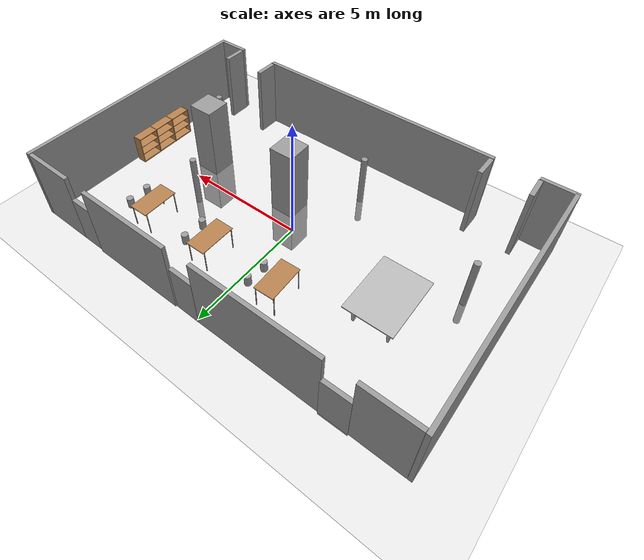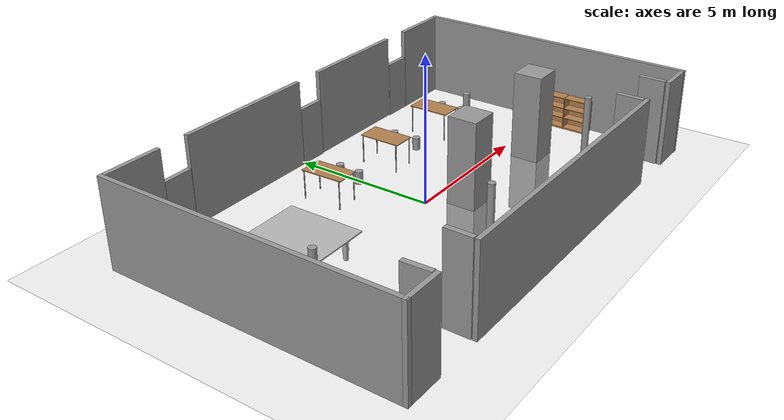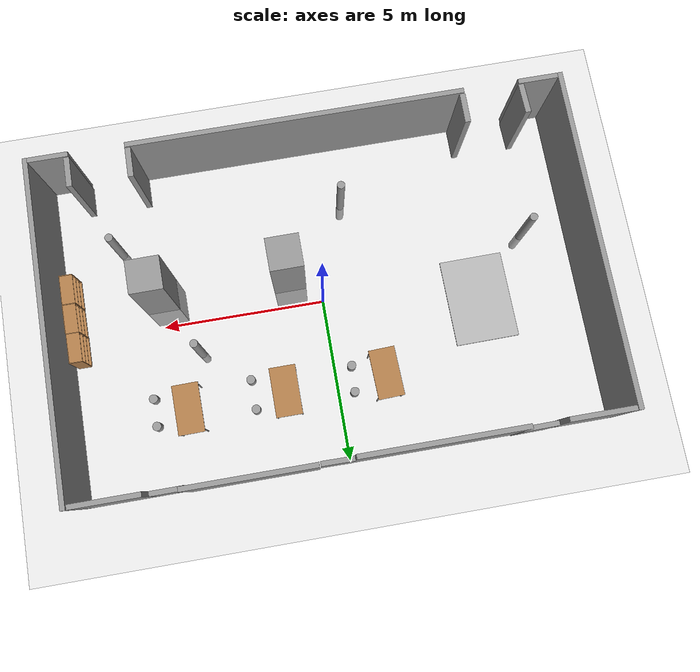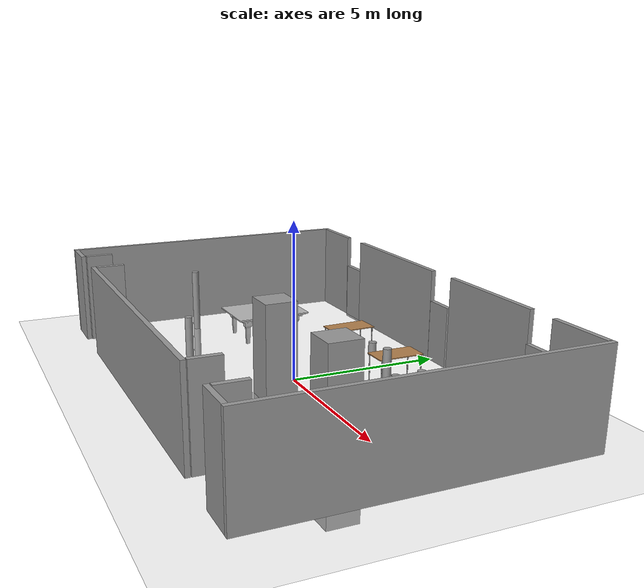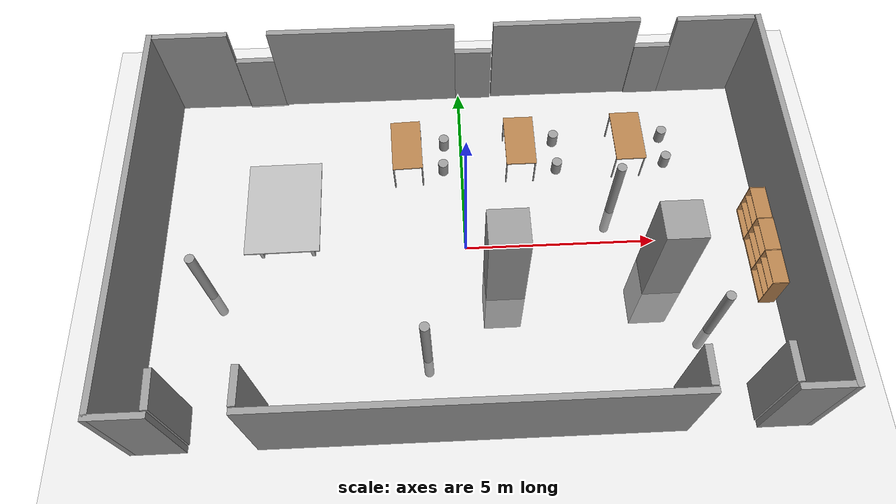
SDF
<sdf version="1.6">
 <world name="default">
  <light name="sun" type="directional">
   <pose>0 0 10 0 -0 0</pose>
   <diffuse>0.8 0.8 0.8 1</diffuse>
   <specular>0.2 0.2 0.2 1</specular>
   <attenuation>
    <range>1000</range>
    <constant>0.9</constant>
    <linear>0.01</linear>
    <quadratic>0.001</quadratic>
   </attenuation>
   <direction>-0.5 0.1 -0.9</direction>
  </light>
  <model name="ground_plane">
   <static>1</static>
   <link name="link">
    <collision name="collision">
     <geometry><plane><normal>0 0 1</normal><size>100 100</size></plane></geometry>
     <surface><friction><ode><mu>100</mu><mu2>50</mu2></ode></friction></surface>
    </collision>
    <visual name="visual">
     <cast_shadows>0</cast_shadows>
     <geometry><plane><normal>0 0 1</normal><size>100 100</size></plane></geometry>
     <material>
      <script><uri>file://media/materials/scripts/gazebo.material</uri><name>Gazebo/Grey</name></script>
     </material>
    </visual>
   </link>
  </model>
  <gravity>0 0 -9.8</gravity>
  <magnetic_field>6e-06 2.3e-05 -4.2e-05</magnetic_field>
  <atmosphere type="adiabatic"/>
  <physics name="default_physics" default="0" type="ode">
   <max_step_size>0.001</max_step_size>
   <real_time_factor>1</real_time_factor>
   <real_time_update_rate>1000</real_time_update_rate>
  </physics>
  <scene><ambient>0.4 0.4 0.4 1</ambient><background>0.7 0.7 0.7 1</background><shadows>1</shadows></scene>
  <audio><device>default</device></audio>
  <spherical_coordinates>
   <surface_model>EARTH_WGS84</surface_model>
   <latitude_deg>0</latitude_deg>
   <longitude_deg>0</longitude_deg>
   <elevation>0</elevation>
   <heading_deg>0</heading_deg>
  </spherical_coordinates>
  <model name="5">
   <link name="Door_0">
    <pose>-6.8 -4.45535 0 0 -0 1.60426</pose>
    <visual name="Door_0_Visual">
     <pose>0 0 1.5 0 -0 0</pose>
     <geometry><box><size>0.9 0.17 3</size></box></geometry>
     <material>
      <script><uri>file://media/materials/scripts/gazebo.material</uri><name>Gazebo/Grey</name></script>
     </material>
    </visual>
    <collision name="Door_0_Collision">
     <pose>0 0 1.5 0 -0 0</pose>
     <geometry><box><size>0.9 0.17 3</size></box></geometry>
     <surface>
      <friction>
       <ode><mu>1</mu><mu2>1</mu2><fdir1>0 0 0</fdir1><slip1>0</slip1><slip2>0</slip2></ode>
       <torsional>
        <coefficient>1</coefficient>
        <patch_radius>0</patch_radius>
        <surface_radius>0</surface_radius>
        <use_patch_radius>1</use_patch_radius>
        <ode><slip>0</slip></ode>
       </torsional>
      </friction>
      <bounce><restitution_coefficient>0</restitution_coefficient><threshold>1e+06</threshold></bounce>
      <contact>
       <collide_without_contact>0</collide_without_contact>
       <collide_without_contact_bitmask>1</collide_without_contact_bitmask>
       <collide_bitmask>1</collide_bitmask>
       <ode>
        <soft_cfm>0</soft_cfm>
        <soft_erp>0.2</soft_erp>
        <kp>1e+13</kp>
        <kd>1</kd>
        <max_vel>0.01</max_vel>
        <min_depth>0</min_depth>
       </ode>
       <bullet>
        <split_impulse>1</split_impulse>
        <split_impulse_penetration_threshold>-0.01</split_impulse_penetration_threshold>
        <soft_cfm>0</soft_cfm>
        <soft_erp>0.2</soft_erp>
        <kp>1e+13</kp>
        <kd>1</kd>
       </bullet>
      </contact>
     </surface>
    </collision>
   </link>
   <link name="Door_1">
    <pose>-5 -4.45535 0 0 0 -1.57995</pose>
    <visual name="Door_1_Visual">
     <pose>0 0 1.5 0 -0 0</pose>
     <geometry><box><size>0.9 0.17 3</size></box></geometry>
     <material>
      <script><uri>file://media/materials/scripts/gazebo.material</uri><name>Gazebo/Grey</name></script>
     </material>
    </visual>
    <collision name="Door_1_Collision">
     <pose>0 0 1.5 0 -0 0</pose>
     <geometry><box><size>0.9 0.17 3</size></box></geometry>
     <surface>
      <friction>
       <ode><mu>1</mu><mu2>1</mu2><fdir1>0 0 0</fdir1><slip1>0</slip1><slip2>0</slip2></ode>
       <torsional>
        <coefficient>1</coefficient>
        <patch_radius>0</patch_radius>
        <surface_radius>0</surface_radius>
        <use_patch_radius>1</use_patch_radius>
        <ode><slip>0</slip></ode>
       </torsional>
      </friction>
      <bounce><restitution_coefficient>0</restitution_coefficient><threshold>1e+06</threshold></bounce>
      <contact>
       <collide_without_contact>0</collide_without_contact>
       <collide_without_contact_bitmask>1</collide_without_contact_bitmask>
       <collide_bitmask>1</collide_bitmask>
       <ode>
        <soft_cfm>0</soft_cfm>
        <soft_erp>0.2</soft_erp>
        <kp>1e+13</kp>
        <kd>1</kd>
        <max_vel>0.01</max_vel>
        <min_depth>0</min_depth>
       </ode>
       <bullet>
        <split_impulse>1</split_impulse>
        <split_impulse_penetration_threshold>-0.01</split_impulse_penetration_threshold>
        <soft_cfm>0</soft_cfm>
        <soft_erp>0.2</soft_erp>
        <kp>1e+13</kp>
        <kd>1</kd>
       </bullet>
      </contact>
     </surface>
    </collision>
   </link>
   <link name="Door_2">
    <pose>5 -4.45535 0 0 -0 1.55702</pose>
    <visual name="Door_2_Visual">
     <pose>0 0 1.5 0 -0 0</pose>
     <geometry><box><size>0.9 0.17 3</size></box></geometry>
     <material>
      <script><uri>file://media/materials/scripts/gazebo.material</uri><name>Gazebo/Grey</name></script>
     </material>
    </visual>
    <collision name="Door_2_Collision">
     <pose>0 0 1.5 0 -0 0</pose>
     <geometry><box><size>0.9 0.17 3</size></box></geometry>
     <surface>
      <friction>
       <ode><mu>1</mu><mu2>1</mu2><fdir1>0 0 0</fdir1><slip1>0</slip1><slip2>0</slip2></ode>
       <torsional>
        <coefficient>1</coefficient>
        <patch_radius>0</patch_radius>
        <surface_radius>0</surface_radius>
        <use_patch_radius>1</use_patch_radius>
        <ode><slip>0</slip></ode>
       </torsional>
      </friction>
      <bounce><restitution_coefficient>0</restitution_coefficient><threshold>1e+06</threshold></bounce>
      <contact>
       <collide_without_contact>0</collide_without_contact>
       <collide_without_contact_bitmask>1</collide_without_contact_bitmask>
       <collide_bitmask>1</collide_bitmask>
       <ode>
        <soft_cfm>0</soft_cfm>
        <soft_erp>0.2</soft_erp>
        <kp>1e+13</kp>
        <kd>1</kd>
        <max_vel>0.01</max_vel>
        <min_depth>0</min_depth>
       </ode>
       <bullet>
        <split_impulse>1</split_impulse>
        <split_impulse_penetration_threshold>-0.01</split_impulse_penetration_threshold>
        <soft_cfm>0</soft_cfm>
        <soft_erp>0.2</soft_erp>
        <kp>1e+13</kp>
        <kd>1</kd>
       </bullet>
      </contact>
     </surface>
    </collision>
   </link>
   <link name="Door_3">
    <pose>6.8 -4.45535 0 0 0 -1.58271</pose>
    <visual name="Door_3_Visual">
     <pose>0 0 1.5 0 -0 0</pose>
     <geometry><box><size>0.9 0.17 3</size></box></geometry>
     <material>
      <script><uri>file://media/materials/scripts/gazebo.material</uri><name>Gazebo/Grey</name></script>
     </material>
    </visual>
    <collision name="Door_3_Collision">
     <pose>0 0 1.5 0 -0 0</pose>
     <geometry><box><size>0.9 0.17 3</size></box></geometry>
     <surface>
      <friction>
       <ode><mu>1</mu><mu2>1</mu2><fdir1>0 0 0</fdir1><slip1>0</slip1><slip2>0</slip2></ode>
       <torsional>
        <coefficient>1</coefficient>
        <patch_radius>0</patch_radius>
        <surface_radius>0</surface_radius>
        <use_patch_radius>1</use_patch_radius>
        <ode><slip>0</slip></ode>
       </torsional>
      </friction>
      <bounce><restitution_coefficient>0</restitution_coefficient><threshold>1e+06</threshold></bounce>
      <contact>
       <collide_without_contact>0</collide_without_contact>
       <collide_without_contact_bitmask>1</collide_without_contact_bitmask>
       <collide_bitmask>1</collide_bitmask>
       <ode>
        <soft_cfm>0</soft_cfm>
        <soft_erp>0.2</soft_erp>
        <kp>1e+13</kp>
        <kd>1</kd>
        <max_vel>0.01</max_vel>
        <min_depth>0</min_depth>
       </ode>
       <bullet>
        <split_impulse>1</split_impulse>
        <split_impulse_penetration_threshold>-0.01</split_impulse_penetration_threshold>
        <soft_cfm>0</soft_cfm>
        <soft_erp>0.2</soft_erp>
        <kp>1e+13</kp>
        <kd>1</kd>
       </bullet>
      </contact>
     </surface>
    </collision>
   </link>
   <link name="Wall_10">
    <pose>7.34 -5.00535 0 0 -0 0</pose>
    <visual name="Wall_10_Visual">
     <pose>0 0 1.5 0 -0 0</pose>
     <geometry><box><size>1.2 0.15 3</size></box></geometry>
     <material>
      <script><uri>file://media/materials/scripts/gazebo.material</uri><name>Gazebo/Grey</name></script>
      <ambient>1 1 1 1</ambient>
     </material>
     <meta><layer>0</layer></meta>
    </visual>
    <collision name="Wall_10_Collision">
     <pose>0 0 1.5 0 -0 0</pose>
     <geometry><box><size>1.2 0.15 3</size></box></geometry>
     <surface>
      <friction>
       <ode><mu>1</mu><mu2>1</mu2><fdir1>0 0 0</fdir1><slip1>0</slip1><slip2>0</slip2></ode>
       <torsional>
        <coefficient>1</coefficient>
        <patch_radius>0</patch_radius>
        <surface_radius>0</surface_radius>
        <use_patch_radius>1</use_patch_radius>
        <ode><slip>0</slip></ode>
       </torsional>
      </friction>
      <bounce><restitution_coefficient>0</restitution_coefficient><threshold>1e+06</threshold></bounce>
      <contact>
       <collide_without_contact>0</collide_without_contact>
       <collide_without_contact_bitmask>1</collide_without_contact_bitmask>
       <collide_bitmask>1</collide_bitmask>
       <ode>
        <soft_cfm>0</soft_cfm>
        <soft_erp>0.2</soft_erp>
        <kp>1e+13</kp>
        <kd>1</kd>
        <max_vel>0.01</max_vel>
        <min_depth>0</min_depth>
       </ode>
       <bullet>
        <split_impulse>1</split_impulse>
        <split_impulse_penetration_threshold>-0.01</split_impulse_penetration_threshold>
        <soft_cfm>0</soft_cfm>
        <soft_erp>0.2</soft_erp>
        <kp>1e+13</kp>
        <kd>1</kd>
       </bullet>
      </contact>
     </surface>
    </collision>
   </link>
   <link name="Wall_12">
    <pose>8 -0.005352 0 0 -0 1.5708</pose>
    <visual name="Wall_12_Visual">
     <pose>0 0 1.5 0 -0 0</pose>
     <geometry><box><size>10.15 0.15 3</size></box></geometry>
     <material>
      <script><uri>file://media/materials/scripts/gazebo.material</uri><name>Gazebo/Grey</name></script>
      <ambient>1 1 1 1</ambient>
     </material>
     <meta><layer>0</layer></meta>
    </visual>
    <collision name="Wall_12_Collision">
     <pose>0 0 1.5 0 -0 0</pose>
     <geometry><box><size>10.15 0.15 3</size></box></geometry>
     <surface>
      <friction>
       <ode><mu>1</mu><mu2>1</mu2><fdir1>0 0 0</fdir1><slip1>0</slip1><slip2>0</slip2></ode>
       <torsional>
        <coefficient>1</coefficient>
        <patch_radius>0</patch_radius>
        <surface_radius>0</surface_radius>
        <use_patch_radius>1</use_patch_radius>
        <ode><slip>0</slip></ode>
       </torsional>
      </friction>
      <bounce><restitution_coefficient>0</restitution_coefficient><threshold>1e+06</threshold></bounce>
      <contact>
       <collide_without_contact>0</collide_without_contact>
       <collide_without_contact_bitmask>1</collide_without_contact_bitmask>
       <collide_bitmask>1</collide_bitmask>
       <ode>
        <soft_cfm>0</soft_cfm>
        <soft_erp>0.2</soft_erp>
        <kp>1e+13</kp>
        <kd>1</kd>
        <max_vel>0.01</max_vel>
        <min_depth>0</min_depth>
       </ode>
       <bullet>
        <split_impulse>1</split_impulse>
        <split_impulse_penetration_threshold>-0.01</split_impulse_penetration_threshold>
        <soft_cfm>0</soft_cfm>
        <soft_erp>0.2</soft_erp>
        <kp>1e+13</kp>
        <kd>1</kd>
       </bullet>
      </contact>
     </surface>
    </collision>
   </link>
   <link name="Wall_14">
    <pose>-6.95 4.99465 0 0 -0 0</pose>
    <inertial>
     <inertia><ixx>0</ixx><ixy>0</ixy><ixz>0</ixz><iyy>0</iyy><iyz>0</iyz><izz>0</izz></inertia>
     <mass>0</mass>
    </inertial>
    <visual name="Wall_14_Visual">
     <pose>0 0 1.5 0 -0 0</pose>
     <geometry><box><size>1.92851 0.15 3</size></box></geometry>
     <material>
      <script><uri>file://media/materials/scripts/gazebo.material</uri><name>Gazebo/Grey</name></script>
      <ambient>1 1 1 1</ambient>
     </material>
     <meta><layer>0</layer></meta>
    </visual>
    <collision name="Wall_14_Collision">
     <pose>0 0 1.5 0 -0 0</pose>
     <geometry><box><size>1.92851 0.15 3</size></box></geometry>
     <surface>
      <friction>
       <ode><mu>1</mu><mu2>1</mu2><fdir1>0 0 0</fdir1><slip1>0</slip1><slip2>0</slip2></ode>
       <torsional>
        <coefficient>1</coefficient>
        <patch_radius>0</patch_radius>
        <surface_radius>0</surface_radius>
        <use_patch_radius>1</use_patch_radius>
        <ode><slip>0</slip></ode>
       </torsional>
      </friction>
      <bounce><restitution_coefficient>0</restitution_coefficient><threshold>1e+06</threshold></bounce>
      <contact>
       <collide_without_contact>0</collide_without_contact>
       <collide_without_contact_bitmask>1</collide_without_contact_bitmask>
       <collide_bitmask>1</collide_bitmask>
       <ode>
        <soft_cfm>0</soft_cfm>
        <soft_erp>0.2</soft_erp>
        <kp>1e+13</kp>
        <kd>1</kd>
        <max_vel>0.01</max_vel>
        <min_depth>0</min_depth>
       </ode>
       <bullet>
        <split_impulse>1</split_impulse>
        <split_impulse_penetration_threshold>-0.01</split_impulse_penetration_threshold>
        <soft_cfm>0</soft_cfm>
        <soft_erp>0.2</soft_erp>
        <kp>1e+13</kp>
        <kd>1</kd>
       </bullet>
      </contact>
     </surface>
    </collision>
   </link>
   <link name="Wall_16">
    <pose>-5.46038 5.01485 -0.090835 0 -0 0.010986</pose>
    <inertial>
     <inertia><ixx>0</ixx><ixy>0</ixy><ixz>0</ixz><iyy>0</iyy><iyz>0</iyz><izz>0</izz></inertia>
     <mass>0</mass>
    </inertial>
    <visual name="Wall_16_Visual_0">
     <pose>0 0 1 0 -0 0</pose>
     <geometry><box><size>1.06569 0.15 2</size></box></geometry>
     <material>
      <script><uri>file://media/materials/scripts/gazebo.material</uri><name>Gazebo/Grey</name></script>
      <ambient>1 1 1 1</ambient>
     </material>
     <meta><layer>0</layer></meta>
    </visual>
    <collision name="Wall_16_Collision_0">
     <pose>0 0 1 0 -0 0</pose>
     <geometry><box><size>1.06569 0.15 2</size></box></geometry>
     <surface>
      <friction>
       <ode><mu>1</mu><mu2>1</mu2><fdir1>0 0 0</fdir1><slip1>0</slip1><slip2>0</slip2></ode>
       <torsional>
        <coefficient>1</coefficient>
        <patch_radius>0</patch_radius>
        <surface_radius>0</surface_radius>
        <use_patch_radius>1</use_patch_radius>
        <ode><slip>0</slip></ode>
       </torsional>
      </friction>
      <bounce><restitution_coefficient>0</restitution_coefficient><threshold>1e+06</threshold></bounce>
      <contact>
       <collide_without_contact>0</collide_without_contact>
       <collide_without_contact_bitmask>1</collide_without_contact_bitmask>
       <collide_bitmask>1</collide_bitmask>
       <ode>
        <soft_cfm>0</soft_cfm>
        <soft_erp>0.2</soft_erp>
        <kp>1e+13</kp>
        <kd>1</kd>
        <max_vel>0.01</max_vel>
        <min_depth>0</min_depth>
       </ode>
       <bullet>
        <split_impulse>1</split_impulse>
        <split_impulse_penetration_threshold>-0.01</split_impulse_penetration_threshold>
        <soft_cfm>0</soft_cfm>
        <soft_erp>0.2</soft_erp>
        <kp>1e+13</kp>
        <kd>1</kd>
       </bullet>
      </contact>
     </surface>
    </collision>
   </link>
   <link name="Wall_18">
    <pose>-2.49995 5.00014 0 0 -0 0</pose>
    <inertial>
     <inertia><ixx>0</ixx><ixy>0</ixy><ixz>0</ixz><iyy>0</iyy><iyz>0</iyz><izz>0</izz></inertia>
     <mass>0</mass>
    </inertial>
    <visual name="Wall_18_Visual">
     <pose>0 0 1.5 0 -0 0</pose>
     <geometry><box><size>4.90994 0.15 3</size></box></geometry>
     <material>
      <script><uri>file://media/materials/scripts/gazebo.material</uri><name>Gazebo/Grey</name></script>
      <ambient>1 1 1 1</ambient>
     </material>
     <meta><layer>0</layer></meta>
    </visual>
    <collision name="Wall_18_Collision">
     <pose>0 0 1.5 0 -0 0</pose>
     <geometry><box><size>4.90994 0.15 3</size></box></geometry>
     <surface>
      <friction>
       <ode><mu>1</mu><mu2>1</mu2><fdir1>0 0 0</fdir1><slip1>0</slip1><slip2>0</slip2></ode>
       <torsional>
        <coefficient>1</coefficient>
        <patch_radius>0</patch_radius>
        <surface_radius>0</surface_radius>
        <use_patch_radius>1</use_patch_radius>
        <ode><slip>0</slip></ode>
       </torsional>
      </friction>
      <bounce><restitution_coefficient>0</restitution_coefficient><threshold>1e+06</threshold></bounce>
      <contact>
       <collide_without_contact>0</collide_without_contact>
       <collide_without_contact_bitmask>1</collide_without_contact_bitmask>
       <collide_bitmask>1</collide_bitmask>
       <ode>
        <soft_cfm>0</soft_cfm>
        <soft_erp>0.2</soft_erp>
        <kp>1e+13</kp>
        <kd>1</kd>
        <max_vel>0.01</max_vel>
        <min_depth>0</min_depth>
       </ode>
       <bullet>
        <split_impulse>1</split_impulse>
        <split_impulse_penetration_threshold>-0.01</split_impulse_penetration_threshold>
        <soft_cfm>0</soft_cfm>
        <soft_erp>0.2</soft_erp>
        <kp>1e+13</kp>
        <kd>1</kd>
       </bullet>
      </contact>
     </surface>
    </collision>
   </link>
   <link name="Wall_2">
    <pose>-7.4 -5.00535 0 0 -0 0</pose>
    <visual name="Wall_2_Visual">
     <pose>0 0 1.5 0 -0 0</pose>
     <geometry><box><size>1.35 0.15 3</size></box></geometry>
     <material>
      <script><uri>file://media/materials/scripts/gazebo.material</uri><name>Gazebo/Grey</name></script>
      <ambient>1 1 1 1</ambient>
     </material>
     <meta><layer>0</layer></meta>
    </visual>
    <collision name="Wall_2_Collision">
     <pose>0 0 1.5 0 -0 0</pose>
     <geometry><box><size>1.35 0.15 3</size></box></geometry>
     <surface>
      <friction>
       <ode><mu>1</mu><mu2>1</mu2><fdir1>0 0 0</fdir1><slip1>0</slip1><slip2>0</slip2></ode>
       <torsional>
        <coefficient>1</coefficient>
        <patch_radius>0</patch_radius>
        <surface_radius>0</surface_radius>
        <use_patch_radius>1</use_patch_radius>
        <ode><slip>0</slip></ode>
       </torsional>
      </friction>
      <bounce><restitution_coefficient>0</restitution_coefficient><threshold>1e+06</threshold></bounce>
      <contact>
       <collide_without_contact>0</collide_without_contact>
       <collide_without_contact_bitmask>1</collide_without_contact_bitmask>
       <collide_bitmask>1</collide_bitmask>
       <ode>
        <soft_cfm>0</soft_cfm>
        <soft_erp>0.2</soft_erp>
        <kp>1e+13</kp>
        <kd>1</kd>
        <max_vel>0.01</max_vel>
        <min_depth>0</min_depth>
       </ode>
       <bullet>
        <split_impulse>1</split_impulse>
        <split_impulse_penetration_threshold>-0.01</split_impulse_penetration_threshold>
        <soft_cfm>0</soft_cfm>
        <soft_erp>0.2</soft_erp>
        <kp>1e+13</kp>
        <kd>1</kd>
       </bullet>
      </contact>
     </surface>
    </collision>
   </link>
   <link name="Wall_20">
    <pose>0.45 4.99959 0 0 0 -0.010986</pose>
    <inertial>
     <inertia><ixx>0</ixx><ixy>0</ixy><ixz>0</ixz><iyy>0</iyy><iyz>0</iyz><izz>0</izz></inertia>
     <mass>0</mass>
    </inertial>
    <visual name="Wall_20_Visual_0">
     <pose>0 0 1 0 -0 0</pose>
     <geometry><box><size>1.00165 0.15 2</size></box></geometry>
     <material>
      <script><uri>file://media/materials/scripts/gazebo.material</uri><name>Gazebo/Grey</name></script>
      <ambient>1 1 1 1</ambient>
     </material>
     <meta><layer>0</layer></meta>
    </visual>
    <collision name="Wall_20_Collision_0">
     <pose>0 0 1 0 -0 0</pose>
     <geometry><box><size>1.00165 0.15 2</size></box></geometry>
     <surface>
      <friction>
       <ode><mu>1</mu><mu2>1</mu2><fdir1>0 0 0</fdir1><slip1>0</slip1><slip2>0</slip2></ode>
       <torsional>
        <coefficient>1</coefficient>
        <patch_radius>0</patch_radius>
        <surface_radius>0</surface_radius>
        <use_patch_radius>1</use_patch_radius>
        <ode><slip>0</slip></ode>
       </torsional>
      </friction>
      <bounce><restitution_coefficient>0</restitution_coefficient><threshold>1e+06</threshold></bounce>
      <contact>
       <collide_without_contact>0</collide_without_contact>
       <collide_without_contact_bitmask>1</collide_without_contact_bitmask>
       <collide_bitmask>1</collide_bitmask>
       <ode>
        <soft_cfm>0</soft_cfm>
        <soft_erp>0.2</soft_erp>
        <kp>1e+13</kp>
        <kd>1</kd>
        <max_vel>0.01</max_vel>
        <min_depth>0</min_depth>
       </ode>
       <bullet>
        <split_impulse>1</split_impulse>
        <split_impulse_penetration_threshold>-0.01</split_impulse_penetration_threshold>
        <soft_cfm>0</soft_cfm>
        <soft_erp>0.2</soft_erp>
        <kp>1e+13</kp>
        <kd>1</kd>
       </bullet>
      </contact>
     </surface>
    </collision>
   </link>
   <link name="Wall_22">
    <pose>2.93225 5.03398 0 0 -0 0.000503</pose>
    <inertial>
     <inertia><ixx>0</ixx><ixy>0</ixy><ixz>0</ixz><iyy>0</iyy><iyz>0</iyz><izz>0</izz></inertia>
     <mass>0</mass>
    </inertial>
    <visual name="Wall_22_Visual">
     <pose>0 0 1.5 0 -0 0</pose>
     <geometry><box><size>3.89162 0.15 3</size></box></geometry>
     <material>
      <script><uri>file://media/materials/scripts/gazebo.material</uri><name>Gazebo/Grey</name></script>
      <ambient>1 1 1 1</ambient>
     </material>
     <meta><layer>0</layer></meta>
    </visual>
    <collision name="Wall_22_Collision">
     <pose>0 0 1.5 0 -0 0</pose>
     <geometry><box><size>3.89162 0.15 3</size></box></geometry>
     <surface>
      <friction>
       <ode><mu>1</mu><mu2>1</mu2><fdir1>0 0 0</fdir1><slip1>0</slip1><slip2>0</slip2></ode>
       <torsional>
        <coefficient>1</coefficient>
        <patch_radius>0</patch_radius>
        <surface_radius>0</surface_radius>
        <use_patch_radius>1</use_patch_radius>
        <ode><slip>0</slip></ode>
       </torsional>
      </friction>
      <bounce><restitution_coefficient>0</restitution_coefficient><threshold>1e+06</threshold></bounce>
      <contact>
       <collide_without_contact>0</collide_without_contact>
       <collide_without_contact_bitmask>1</collide_without_contact_bitmask>
       <collide_bitmask>1</collide_bitmask>
       <ode>
        <soft_cfm>0</soft_cfm>
        <soft_erp>0.2</soft_erp>
        <kp>1e+13</kp>
        <kd>1</kd>
        <max_vel>0.01</max_vel>
        <min_depth>0</min_depth>
       </ode>
       <bullet>
        <split_impulse>1</split_impulse>
        <split_impulse_penetration_threshold>-0.01</split_impulse_penetration_threshold>
        <soft_cfm>0</soft_cfm>
        <soft_erp>0.2</soft_erp>
        <kp>1e+13</kp>
        <kd>1</kd>
       </bullet>
      </contact>
     </surface>
    </collision>
   </link>
   <link name="Wall_24">
    <pose>5.375 4.99465 0 0 -0 0</pose>
    <inertial>
     <inertia><ixx>0</ixx><ixy>0</ixy><ixz>0</ixz><iyy>0</iyy><iyz>0</iyz><izz>0</izz></inertia>
     <mass>0</mass>
    </inertial>
    <visual name="Wall_24_Visual_0">
     <pose>0 0 1 0 -0 0</pose>
     <geometry><box><size>1.00475 0.15 2</size></box></geometry>
     <material>
      <script><uri>file://media/materials/scripts/gazebo.material</uri><name>Gazebo/Grey</name></script>
      <ambient>1 1 1 1</ambient>
     </material>
     <meta><layer>0</layer></meta>
    </visual>
    <collision name="Wall_24_Collision_0">
     <pose>0 0 1 0 -0 0</pose>
     <geometry><box><size>1.00475 0.15 2</size></box></geometry>
     <surface>
      <friction>
       <ode><mu>1</mu><mu2>1</mu2><fdir1>0 0 0</fdir1><slip1>0</slip1><slip2>0</slip2></ode>
       <torsional>
        <coefficient>1</coefficient>
        <patch_radius>0</patch_radius>
        <surface_radius>0</surface_radius>
        <use_patch_radius>1</use_patch_radius>
        <ode><slip>0</slip></ode>
       </torsional>
      </friction>
      <bounce><restitution_coefficient>0</restitution_coefficient><threshold>1e+06</threshold></bounce>
      <contact>
       <collide_without_contact>0</collide_without_contact>
       <collide_without_contact_bitmask>1</collide_without_contact_bitmask>
       <collide_bitmask>1</collide_bitmask>
       <ode>
        <soft_cfm>0</soft_cfm>
        <soft_erp>0.2</soft_erp>
        <kp>1e+13</kp>
        <kd>1</kd>
        <max_vel>0.01</max_vel>
        <min_depth>0</min_depth>
       </ode>
       <bullet>
        <split_impulse>1</split_impulse>
        <split_impulse_penetration_threshold>-0.01</split_impulse_penetration_threshold>
        <soft_cfm>0</soft_cfm>
        <soft_erp>0.2</soft_erp>
        <kp>1e+13</kp>
        <kd>1</kd>
       </bullet>
      </contact>
     </surface>
    </collision>
   </link>
   <link name="Wall_26">
    <pose>6.875 4.99465 0 0 -0 0</pose>
    <inertial>
     <inertia><ixx>0</ixx><ixy>0</ixy><ixz>0</ixz><iyy>0</iyy><iyz>0</iyz><izz>0</izz></inertia>
     <mass>0</mass>
    </inertial>
    <visual name="Wall_26_Visual">
     <pose>0 0 1.5 0 -0 0</pose>
     <geometry><box><size>2.0482 0.15 3</size></box></geometry>
     <material>
      <script><uri>file://media/materials/scripts/gazebo.material</uri><name>Gazebo/Grey</name></script>
      <ambient>1 1 1 1</ambient>
     </material>
     <meta><layer>0</layer></meta>
    </visual>
    <collision name="Wall_26_Collision">
     <pose>0 0 1.5 0 -0 0</pose>
     <geometry><box><size>2.0482 0.15 3</size></box></geometry>
     <surface>
      <friction>
       <ode><mu>1</mu><mu2>1</mu2><fdir1>0 0 0</fdir1><slip1>0</slip1><slip2>0</slip2></ode>
       <torsional>
        <coefficient>1</coefficient>
        <patch_radius>0</patch_radius>
        <surface_radius>0</surface_radius>
        <use_patch_radius>1</use_patch_radius>
        <ode><slip>0</slip></ode>
       </torsional>
      </friction>
      <bounce><restitution_coefficient>0</restitution_coefficient><threshold>1e+06</threshold></bounce>
      <contact>
       <collide_without_contact>0</collide_without_contact>
       <collide_without_contact_bitmask>1</collide_without_contact_bitmask>
       <collide_bitmask>1</collide_bitmask>
       <ode>
        <soft_cfm>0</soft_cfm>
        <soft_erp>0.2</soft_erp>
        <kp>1e+13</kp>
        <kd>1</kd>
        <max_vel>0.01</max_vel>
        <min_depth>0</min_depth>
       </ode>
       <bullet>
        <split_impulse>1</split_impulse>
        <split_impulse_penetration_threshold>-0.01</split_impulse_penetration_threshold>
        <soft_cfm>0</soft_cfm>
        <soft_erp>0.2</soft_erp>
        <kp>1e+13</kp>
        <kd>1</kd>
       </bullet>
      </contact>
     </surface>
    </collision>
   </link>
   <link name="Wall_4">
    <pose>-8 -0.005353 0 0 -0 1.5708</pose>
    <inertial>
     <mass>1</mass>
     <inertia><ixx>1</ixx><ixy>0</ixy><ixz>0</ixz><iyy>1</iyy><iyz>0</iyz><izz>1</izz></inertia>
    </inertial>
    <visual name="Wall_4_Visual">
     <pose>0 0 1.5 0 -0 0</pose>
     <geometry><box><size>10.15 0.15 3</size></box></geometry>
     <material>
      <script><uri>file://media/materials/scripts/gazebo.material</uri><name>Gazebo/Grey</name></script>
      <ambient>1 1 1 1</ambient>
      <shader type="vertex"><normal_map>__default__</normal_map></shader>
     </material>
     <meta><layer>0</layer></meta>
    </visual>
    <collision name="Wall_4_Collision">
     <pose>0 0 1.5 0 -0 0</pose>
     <geometry><box><size>10.15 0.15 3</size></box></geometry>
     <surface>
      <friction>
       <ode><mu>1</mu><mu2>1</mu2><fdir1>0 0 0</fdir1><slip1>0</slip1><slip2>0</slip2></ode>
       <torsional>
        <coefficient>1</coefficient>
        <patch_radius>0</patch_radius>
        <surface_radius>0</surface_radius>
        <use_patch_radius>1</use_patch_radius>
        <ode><slip>0</slip></ode>
       </torsional>
      </friction>
      <bounce><restitution_coefficient>0</restitution_coefficient><threshold>1e+06</threshold></bounce>
      <contact>
       <collide_without_contact>0</collide_without_contact>
       <collide_without_contact_bitmask>1</collide_without_contact_bitmask>
       <collide_bitmask>1</collide_bitmask>
       <ode>
        <soft_cfm>0</soft_cfm>
        <soft_erp>0.2</soft_erp>
        <kp>1e+13</kp>
        <kd>1</kd>
        <max_vel>0.01</max_vel>
        <min_depth>0</min_depth>
       </ode>
       <bullet>
        <split_impulse>1</split_impulse>
        <split_impulse_penetration_threshold>-0.01</split_impulse_penetration_threshold>
        <soft_cfm>0</soft_cfm>
        <soft_erp>0.2</soft_erp>
        <kp>1e+13</kp>
        <kd>1</kd>
       </bullet>
      </contact>
     </surface>
    </collision>
   </link>
   <link name="Wall_8">
    <pose>0 -5.00535 0 0 -0 0</pose>
    <visual name="Wall_8_Visual">
     <pose>0 0 1.5 0 -0 0</pose>
     <geometry><box><size>10.15 0.15 3</size></box></geometry>
     <material>
      <script><uri>file://media/materials/scripts/gazebo.material</uri><name>Gazebo/Grey</name></script>
      <ambient>1 1 1 1</ambient>
     </material>
     <meta><layer>0</layer></meta>
    </visual>
    <collision name="Wall_8_Collision">
     <pose>0 0 1.5 0 -0 0</pose>
     <geometry><box><size>10.15 0.15 3</size></box></geometry>
     <surface>
      <friction>
       <ode><mu>1</mu><mu2>1</mu2><fdir1>0 0 0</fdir1><slip1>0</slip1><slip2>0</slip2></ode>
       <torsional>
        <coefficient>1</coefficient>
        <patch_radius>0</patch_radius>
        <surface_radius>0</surface_radius>
        <use_patch_radius>1</use_patch_radius>
        <ode><slip>0</slip></ode>
       </torsional>
      </friction>
      <bounce><restitution_coefficient>0</restitution_coefficient><threshold>1e+06</threshold></bounce>
      <contact>
       <collide_without_contact>0</collide_without_contact>
       <collide_without_contact_bitmask>1</collide_without_contact_bitmask>
       <collide_bitmask>1</collide_bitmask>
       <ode>
        <soft_cfm>0</soft_cfm>
        <soft_erp>0.2</soft_erp>
        <kp>1e+13</kp>
        <kd>1</kd>
        <max_vel>0.01</max_vel>
        <min_depth>0</min_depth>
       </ode>
       <bullet>
        <split_impulse>1</split_impulse>
        <split_impulse_penetration_threshold>-0.01</split_impulse_penetration_threshold>
        <soft_cfm>0</soft_cfm>
        <soft_erp>0.2</soft_erp>
        <kp>1e+13</kp>
        <kd>1</kd>
       </bullet>
      </contact>
     </surface>
    </collision>
   </link>
   <link name="link_10">
    <inertial>
     <mass>0.189527</mass>
     <inertia>
      <ixx>0.168646</ixx>
      <ixy>0</ixy>
      <ixz>0</ixz>
      <iyy>0.168646</iyy>
      <iyz>0</iyz>
      <izz>0.00137469</izz>
     </inertia>
    </inertial>
    <pose>3.99203 1.00755 0.5 0 -0 1.57569</pose>
    <visual name="visual">
     <geometry><cylinder><radius>0.120443</radius><length>3.26104</length></cylinder></geometry>
     <material>
      <lighting>1</lighting>
      <script><uri>file://media/materials/scripts/gazebo.material</uri><name>Gazebo/Grey</name></script>
     </material>
    </visual>
    <collision name="collision">
     <geometry><cylinder><radius>0.120443</radius><length>3.26104</length></cylinder></geometry>
     <surface>
      <friction>
       <ode><mu>1</mu><mu2>1</mu2><fdir1>0 0 0</fdir1><slip1>0</slip1><slip2>0</slip2></ode>
       <torsional>
        <coefficient>1</coefficient>
        <patch_radius>0</patch_radius>
        <surface_radius>0</surface_radius>
        <use_patch_radius>1</use_patch_radius>
        <ode><slip>0</slip></ode>
       </torsional>
      </friction>
      <bounce><restitution_coefficient>0</restitution_coefficient><threshold>1e+06</threshold></bounce>
      <contact>
       <collide_without_contact>0</collide_without_contact>
       <collide_without_contact_bitmask>1</collide_without_contact_bitmask>
       <collide_bitmask>1</collide_bitmask>
       <ode>
        <soft_cfm>0</soft_cfm>
        <soft_erp>0.2</soft_erp>
        <kp>1e+13</kp>
        <kd>1</kd>
        <max_vel>0.01</max_vel>
        <min_depth>0</min_depth>
       </ode>
       <bullet>
        <split_impulse>1</split_impulse>
        <split_impulse_penetration_threshold>-0.01</split_impulse_penetration_threshold>
        <soft_cfm>0</soft_cfm>
        <soft_erp>0.2</soft_erp>
        <kp>1e+13</kp>
        <kd>1</kd>
       </bullet>
      </contact>
     </surface>
    </collision>
   </link>
   <link name="link_10_clone">
    <inertial>
     <mass>0.189527</mass>
     <inertia>
      <ixx>0.168646</ixx>
      <ixy>0</ixy>
      <ixz>0</ixz>
      <iyy>0.168646</iyy>
      <iyz>0</iyz>
      <izz>0.00137469</izz>
     </inertia>
    </inertial>
    <pose>6.03211 -2.55608 0.5 0 0 -3.13181</pose>
    <visual name="visual">
     <geometry><cylinder><radius>0.120443</radius><length>3.26104</length></cylinder></geometry>
     <material>
      <lighting>1</lighting>
      <script><uri>file://media/materials/scripts/gazebo.material</uri><name>Gazebo/Grey</name></script>
      <shader type="pixel"/>
     </material>
    </visual>
    <collision name="collision">
     <geometry><cylinder><radius>0.120443</radius><length>3.26104</length></cylinder></geometry>
     <surface>
      <friction>
       <ode><mu>1</mu><mu2>1</mu2><fdir1>0 0 0</fdir1><slip1>0</slip1><slip2>0</slip2></ode>
       <torsional>
        <coefficient>1</coefficient>
        <patch_radius>0</patch_radius>
        <surface_radius>0</surface_radius>
        <use_patch_radius>1</use_patch_radius>
        <ode><slip>0</slip></ode>
       </torsional>
      </friction>
      <bounce><restitution_coefficient>0</restitution_coefficient><threshold>1e+06</threshold></bounce>
      <contact>
       <collide_without_contact>0</collide_without_contact>
       <collide_without_contact_bitmask>1</collide_without_contact_bitmask>
       <collide_bitmask>1</collide_bitmask>
       <ode>
        <soft_cfm>0</soft_cfm>
        <soft_erp>0.2</soft_erp>
        <kp>1e+13</kp>
        <kd>1</kd>
        <max_vel>0.01</max_vel>
        <min_depth>0</min_depth>
       </ode>
       <bullet>
        <split_impulse>1</split_impulse>
        <split_impulse_penetration_threshold>-0.01</split_impulse_penetration_threshold>
        <soft_cfm>0</soft_cfm>
        <soft_erp>0.2</soft_erp>
        <kp>1e+13</kp>
        <kd>1</kd>
       </bullet>
      </contact>
     </surface>
    </collision>
   </link>
   <link name="link_10_clone_0">
    <inertial>
     <mass>0.189527</mass>
     <inertia>
      <ixx>0.168646</ixx>
      <ixy>0</ixy>
      <ixz>0</ixz>
      <iyy>0.168646</iyy>
      <iyz>0</iyz>
      <izz>0.00137469</izz>
     </inertia>
    </inertial>
    <pose>-1.03893 -3.00419 0.5 0 0 -3.13181</pose>
    <visual name="visual">
     <geometry><cylinder><radius>0.120443</radius><length>3.26104</length></cylinder></geometry>
     <material>
      <lighting>1</lighting>
      <script><uri>file://media/materials/scripts/gazebo.material</uri><name>Gazebo/Grey</name></script>
      <shader type="pixel"/>
     </material>
    </visual>
    <collision name="collision">
     <geometry><cylinder><radius>0.120443</radius><length>3.26104</length></cylinder></geometry>
     <surface>
      <friction>
       <ode><mu>1</mu><mu2>1</mu2><fdir1>0 0 0</fdir1><slip1>0</slip1><slip2>0</slip2></ode>
       <torsional>
        <coefficient>1</coefficient>
        <patch_radius>0</patch_radius>
        <surface_radius>0</surface_radius>
        <use_patch_radius>1</use_patch_radius>
        <ode><slip>0</slip></ode>
       </torsional>
      </friction>
      <bounce><restitution_coefficient>0</restitution_coefficient><threshold>1e+06</threshold></bounce>
      <contact>
       <collide_without_contact>0</collide_without_contact>
       <collide_without_contact_bitmask>1</collide_without_contact_bitmask>
       <collide_bitmask>1</collide_bitmask>
       <ode>
        <soft_cfm>0</soft_cfm>
        <soft_erp>0.2</soft_erp>
        <kp>1e+13</kp>
        <kd>1</kd>
        <max_vel>0.01</max_vel>
        <min_depth>0</min_depth>
       </ode>
       <bullet>
        <split_impulse>1</split_impulse>
        <split_impulse_penetration_threshold>-0.01</split_impulse_penetration_threshold>
        <soft_cfm>0</soft_cfm>
        <soft_erp>0.2</soft_erp>
        <kp>1e+13</kp>
        <kd>1</kd>
       </bullet>
      </contact>
     </surface>
    </collision>
   </link>
   <link name="link_10_clone_1">
    <inertial>
     <mass>0.189527</mass>
     <inertia>
      <ixx>0.168646</ixx>
      <ixy>0</ixy>
      <ixz>0</ixz>
      <iyy>0.168646</iyy>
      <iyz>0</iyz>
      <izz>0.00137469</izz>
     </inertia>
    </inertial>
    <pose>-6.52605 -1.05414 0.5 0 0 -3.13181</pose>
    <visual name="visual">
     <geometry><cylinder><radius>0.120443</radius><length>3.26104</length></cylinder></geometry>
     <material>
      <lighting>1</lighting>
      <script><uri>file://media/materials/scripts/gazebo.material</uri><name>Gazebo/Grey</name></script>
      <shader type="pixel"/>
     </material>
    </visual>
    <collision name="collision">
     <geometry><cylinder><radius>0.120443</radius><length>3.26104</length></cylinder></geometry>
     <surface>
      <friction>
       <ode><mu>1</mu><mu2>1</mu2><fdir1>0 0 0</fdir1><slip1>0</slip1><slip2>0</slip2></ode>
       <torsional>
        <coefficient>1</coefficient>
        <patch_radius>0</patch_radius>
        <surface_radius>0</surface_radius>
        <use_patch_radius>1</use_patch_radius>
        <ode><slip>0</slip></ode>
       </torsional>
      </friction>
      <bounce><restitution_coefficient>0</restitution_coefficient><threshold>1e+06</threshold></bounce>
      <contact>
       <collide_without_contact>0</collide_without_contact>
       <collide_without_contact_bitmask>1</collide_without_contact_bitmask>
       <collide_bitmask>1</collide_bitmask>
       <ode>
        <soft_cfm>0</soft_cfm>
        <soft_erp>0.2</soft_erp>
        <kp>1e+13</kp>
        <kd>1</kd>
        <max_vel>0.01</max_vel>
        <min_depth>0</min_depth>
       </ode>
       <bullet>
        <split_impulse>1</split_impulse>
        <split_impulse_penetration_threshold>-0.01</split_impulse_penetration_threshold>
        <soft_cfm>0</soft_cfm>
        <soft_erp>0.2</soft_erp>
        <kp>1e+13</kp>
        <kd>1</kd>
       </bullet>
      </contact>
     </surface>
    </collision>
   </link>
   <link name="link_13">
    <inertial>
     <mass>0.0313183</mass>
     <inertia>
      <ixx>0.000638939</ixx>
      <ixy>0</ixy>
      <ixz>0</ixz>
      <iyy>0.000638939</iyy>
      <iyz>0</iyz>
      <izz>0.0002788</izz>
     </inertia>
    </inertial>
    <pose>-0.431774 3.02424 0.5 0 -0 1.57569</pose>
    <visual name="visual">
     <geometry><cylinder><radius>0.133433</radius><length>0.437499</length></cylinder></geometry>
     <material>
      <lighting>1</lighting>
      <script><uri>file://media/materials/scripts/gazebo.material</uri><name>Gazebo/Grey</name></script>
     </material>
    </visual>
    <collision name="collision">
     <geometry><cylinder><radius>0.133433</radius><length>0.437499</length></cylinder></geometry>
     <surface>
      <friction>
       <ode><mu>1</mu><mu2>1</mu2><fdir1>0 0 0</fdir1><slip1>0</slip1><slip2>0</slip2></ode>
       <torsional>
        <coefficient>1</coefficient>
        <patch_radius>0</patch_radius>
        <surface_radius>0</surface_radius>
        <use_patch_radius>1</use_patch_radius>
        <ode><slip>0</slip></ode>
       </torsional>
      </friction>
      <bounce><restitution_coefficient>0</restitution_coefficient><threshold>1e+06</threshold></bounce>
      <contact>
       <collide_without_contact>0</collide_without_contact>
       <collide_without_contact_bitmask>1</collide_without_contact_bitmask>
       <collide_bitmask>1</collide_bitmask>
       <ode>
        <soft_cfm>0</soft_cfm>
        <soft_erp>0.2</soft_erp>
        <kp>1e+13</kp>
        <kd>1</kd>
        <max_vel>0.01</max_vel>
        <min_depth>0</min_depth>
       </ode>
       <bullet>
        <split_impulse>1</split_impulse>
        <split_impulse_penetration_threshold>-0.01</split_impulse_penetration_threshold>
        <soft_cfm>0</soft_cfm>
        <soft_erp>0.2</soft_erp>
        <kp>1e+13</kp>
        <kd>1</kd>
       </bullet>
      </contact>
     </surface>
    </collision>
   </link>
   <link name="link_13_clone">
    <inertial>
     <mass>0.0313183</mass>
     <inertia>
      <ixx>0.000638939</ixx>
      <ixy>0</ixy>
      <ixz>0</ixz>
      <iyy>0.000638939</iyy>
      <iyz>0</iyz>
      <izz>0.0002788</izz>
     </inertia>
    </inertial>
    <pose>-0.473274 2.22757 0.5 0 0 -3.13181</pose>
    <visual name="visual">
     <geometry><cylinder><radius>0.133433</radius><length>0.437499</length></cylinder></geometry>
     <material>
      <lighting>1</lighting>
      <script><uri>file://media/materials/scripts/gazebo.material</uri><name>Gazebo/Grey</name></script>
      <shader type="pixel"/>
     </material>
    </visual>
    <collision name="collision">
     <geometry><cylinder><radius>0.133433</radius><length>0.437499</length></cylinder></geometry>
     <surface>
      <friction>
       <ode><mu>1</mu><mu2>1</mu2><fdir1>0 0 0</fdir1><slip1>0</slip1><slip2>0</slip2></ode>
       <torsional>
        <coefficient>1</coefficient>
        <patch_radius>0</patch_radius>
        <surface_radius>0</surface_radius>
        <use_patch_radius>1</use_patch_radius>
        <ode><slip>0</slip></ode>
       </torsional>
      </friction>
      <bounce><restitution_coefficient>0</restitution_coefficient><threshold>1e+06</threshold></bounce>
      <contact>
       <collide_without_contact>0</collide_without_contact>
       <collide_without_contact_bitmask>1</collide_without_contact_bitmask>
       <collide_bitmask>1</collide_bitmask>
       <ode>
        <soft_cfm>0</soft_cfm>
        <soft_erp>0.2</soft_erp>
        <kp>1e+13</kp>
        <kd>1</kd>
        <max_vel>0.01</max_vel>
        <min_depth>0</min_depth>
       </ode>
       <bullet>
        <split_impulse>1</split_impulse>
        <split_impulse_penetration_threshold>-0.01</split_impulse_penetration_threshold>
        <soft_cfm>0</soft_cfm>
        <soft_erp>0.2</soft_erp>
        <kp>1e+13</kp>
        <kd>1</kd>
       </bullet>
      </contact>
     </surface>
    </collision>
   </link>
   <link name="link_13_clone_0">
    <inertial>
     <mass>0.0313183</mass>
     <inertia>
      <ixx>0.000638939</ixx>
      <ixy>0</ixy>
      <ixz>0</ixz>
      <iyy>0.000638939</iyy>
      <iyz>0</iyz>
      <izz>0.0002788</izz>
     </inertia>
    </inertial>
    <pose>2.58171 3.04263 0.5 0 0 -3.13181</pose>
    <visual name="visual">
     <geometry><cylinder><radius>0.133433</radius><length>0.437499</length></cylinder></geometry>
     <material>
      <lighting>1</lighting>
      <script><uri>file://media/materials/scripts/gazebo.material</uri><name>Gazebo/Grey</name></script>
      <shader type="pixel"/>
     </material>
    </visual>
    <collision name="collision">
     <geometry><cylinder><radius>0.133433</radius><length>0.437499</length></cylinder></geometry>
     <surface>
      <friction>
       <ode><mu>1</mu><mu2>1</mu2><fdir1>0 0 0</fdir1><slip1>0</slip1><slip2>0</slip2></ode>
       <torsional>
        <coefficient>1</coefficient>
        <patch_radius>0</patch_radius>
        <surface_radius>0</surface_radius>
        <use_patch_radius>1</use_patch_radius>
        <ode><slip>0</slip></ode>
       </torsional>
      </friction>
      <bounce><restitution_coefficient>0</restitution_coefficient><threshold>1e+06</threshold></bounce>
      <contact>
       <collide_without_contact>0</collide_without_contact>
       <collide_without_contact_bitmask>1</collide_without_contact_bitmask>
       <collide_bitmask>1</collide_bitmask>
       <ode>
        <soft_cfm>0</soft_cfm>
        <soft_erp>0.2</soft_erp>
        <kp>1e+13</kp>
        <kd>1</kd>
        <max_vel>0.01</max_vel>
        <min_depth>0</min_depth>
       </ode>
       <bullet>
        <split_impulse>1</split_impulse>
        <split_impulse_penetration_threshold>-0.01</split_impulse_penetration_threshold>
        <soft_cfm>0</soft_cfm>
        <soft_erp>0.2</soft_erp>
        <kp>1e+13</kp>
        <kd>1</kd>
       </bullet>
      </contact>
     </surface>
    </collision>
   </link>
   <link name="link_13_clone_1">
    <inertial>
     <mass>0.0313183</mass>
     <inertia>
      <ixx>0.00063894</ixx>
      <ixy>0</ixy>
      <ixz>0</ixz>
      <iyy>0.00063894</iyy>
      <iyz>0</iyz>
      <izz>0.0002788</izz>
     </inertia>
    </inertial>
    <pose>2.6065 2.13919 0.5 0 0 -3.13181</pose>
    <visual name="visual">
     <geometry><cylinder><radius>0.133433</radius><length>0.437499</length></cylinder></geometry>
     <material>
      <lighting>1</lighting>
      <script><uri>file://media/materials/scripts/gazebo.material</uri><name>Gazebo/Grey</name></script>
      <shader type="vertex"><normal_map>__default__</normal_map></shader>
      <ambient>0.3 0.3 0.3 1</ambient>
      <diffuse>0.7 0.7 0.7 1</diffuse>
      <specular>0.01 0.01 0.01 1</specular>
      <emissive>0 0 0 1</emissive>
     </material>
    </visual>
    <collision name="collision">
     <geometry><cylinder><radius>0.133433</radius><length>0.437499</length></cylinder></geometry>
     <surface>
      <friction>
       <ode><mu>1</mu><mu2>1</mu2><fdir1>0 0 0</fdir1><slip1>0</slip1><slip2>0</slip2></ode>
       <torsional>
        <coefficient>1</coefficient>
        <patch_radius>0</patch_radius>
        <surface_radius>0</surface_radius>
        <use_patch_radius>1</use_patch_radius>
        <ode><slip>0</slip></ode>
       </torsional>
      </friction>
      <bounce><restitution_coefficient>0</restitution_coefficient><threshold>1e+06</threshold></bounce>
      <contact>
       <collide_without_contact>0</collide_without_contact>
       <collide_without_contact_bitmask>1</collide_without_contact_bitmask>
       <collide_bitmask>1</collide_bitmask>
       <ode>
        <soft_cfm>0</soft_cfm>
        <soft_erp>0.2</soft_erp>
        <kp>1e+13</kp>
        <kd>1</kd>
        <max_vel>0.01</max_vel>
        <min_depth>0</min_depth>
       </ode>
       <bullet>
        <split_impulse>1</split_impulse>
        <split_impulse_penetration_threshold>-0.01</split_impulse_penetration_threshold>
        <soft_cfm>0</soft_cfm>
        <soft_erp>0.2</soft_erp>
        <kp>1e+13</kp>
        <kd>1</kd>
       </bullet>
      </contact>
     </surface>
    </collision>
   </link>
   <link name="link_13_clone_2">
    <inertial>
     <mass>0.0313183</mass>
     <inertia>
      <ixx>0.000638939</ixx>
      <ixy>0</ixy>
      <ixz>0</ixz>
      <iyy>0.000638939</iyy>
      <iyz>0</iyz>
      <izz>0.0002788</izz>
     </inertia>
    </inertial>
    <pose>5.58438 3.04761 0.5 0 0 -3.13181</pose>
    <visual name="visual">
     <geometry><cylinder><radius>0.133433</radius><length>0.437499</length></cylinder></geometry>
     <material>
      <lighting>1</lighting>
      <script><uri>file://media/materials/scripts/gazebo.material</uri><name>Gazebo/Grey</name></script>
      <shader type="pixel"/>
     </material>
    </visual>
    <collision name="collision">
     <geometry><cylinder><radius>0.133433</radius><length>0.437499</length></cylinder></geometry>
     <surface>
      <friction>
       <ode><mu>1</mu><mu2>1</mu2><fdir1>0 0 0</fdir1><slip1>0</slip1><slip2>0</slip2></ode>
       <torsional>
        <coefficient>1</coefficient>
        <patch_radius>0</patch_radius>
        <surface_radius>0</surface_radius>
        <use_patch_radius>1</use_patch_radius>
        <ode><slip>0</slip></ode>
       </torsional>
      </friction>
      <bounce><restitution_coefficient>0</restitution_coefficient><threshold>1e+06</threshold></bounce>
      <contact>
       <collide_without_contact>0</collide_without_contact>
       <collide_without_contact_bitmask>1</collide_without_contact_bitmask>
       <collide_bitmask>1</collide_bitmask>
       <ode>
        <soft_cfm>0</soft_cfm>
        <soft_erp>0.2</soft_erp>
        <kp>1e+13</kp>
        <kd>1</kd>
        <max_vel>0.01</max_vel>
        <min_depth>0</min_depth>
       </ode>
       <bullet>
        <split_impulse>1</split_impulse>
        <split_impulse_penetration_threshold>-0.01</split_impulse_penetration_threshold>
        <soft_cfm>0</soft_cfm>
        <soft_erp>0.2</soft_erp>
        <kp>1e+13</kp>
        <kd>1</kd>
       </bullet>
      </contact>
     </surface>
    </collision>
   </link>
   <link name="link_13_clone_3">
    <inertial>
     <mass>0.0313183</mass>
     <inertia>
      <ixx>0.000638939</ixx>
      <ixy>0</ixy>
      <ixz>0</ixz>
      <iyy>0.000638939</iyy>
      <iyz>0</iyz>
      <izz>0.0002788</izz>
     </inertia>
    </inertial>
    <pose>5.58067 2.21897 0.5 0 0 -3.13181</pose>
    <visual name="visual">
     <geometry><cylinder><radius>0.133433</radius><length>0.437499</length></cylinder></geometry>
     <material>
      <lighting>1</lighting>
      <script><uri>file://media/materials/scripts/gazebo.material</uri><name>Gazebo/Grey</name></script>
      <shader type="pixel"/>
     </material>
    </visual>
    <collision name="collision">
     <geometry><cylinder><radius>0.133433</radius><length>0.437499</length></cylinder></geometry>
     <surface>
      <friction>
       <ode><mu>1</mu><mu2>1</mu2><fdir1>0 0 0</fdir1><slip1>0</slip1><slip2>0</slip2></ode>
       <torsional>
        <coefficient>1</coefficient>
        <patch_radius>0</patch_radius>
        <surface_radius>0</surface_radius>
        <use_patch_radius>1</use_patch_radius>
        <ode><slip>0</slip></ode>
       </torsional>
      </friction>
      <bounce><restitution_coefficient>0</restitution_coefficient><threshold>1e+06</threshold></bounce>
      <contact>
       <collide_without_contact>0</collide_without_contact>
       <collide_without_contact_bitmask>1</collide_without_contact_bitmask>
       <collide_bitmask>1</collide_bitmask>
       <ode>
        <soft_cfm>0</soft_cfm>
        <soft_erp>0.2</soft_erp>
        <kp>1e+13</kp>
        <kd>1</kd>
        <max_vel>0.01</max_vel>
        <min_depth>0</min_depth>
       </ode>
       <bullet>
        <split_impulse>1</split_impulse>
        <split_impulse_penetration_threshold>-0.01</split_impulse_penetration_threshold>
        <soft_cfm>0</soft_cfm>
        <soft_erp>0.2</soft_erp>
        <kp>1e+13</kp>
        <kd>1</kd>
       </bullet>
      </contact>
     </surface>
    </collision>
   </link>
   <link name="link_7">
    <inertial>
     <mass>4.9684</mass>
     <inertia><ixx>10.6346</ixx><ixy>0</ixy><ixz>0</ixz><iyy>10.6346</iyy><iyz>0</iyz><izz>0.828067</izz></inertia>
    </inertial>
    <pose>0.980818 -1.0177 0.5 0 -0 1.57569</pose>
    <visual name="visual">
     <geometry><box><size>1 1 4.96842</size></box></geometry>
     <material>
      <lighting>1</lighting>
      <script><uri>file://media/materials/scripts/gazebo.material</uri><name>Gazebo/Grey</name></script>
     </material>
    </visual>
    <collision name="collision">
     <geometry><box><size>1 1 4.96842</size></box></geometry>
     <surface>
      <friction>
       <ode><mu>1</mu><mu2>1</mu2><fdir1>0 0 0</fdir1><slip1>0</slip1><slip2>0</slip2></ode>
       <torsional>
        <coefficient>1</coefficient>
        <patch_radius>0</patch_radius>
        <surface_radius>0</surface_radius>
        <use_patch_radius>1</use_patch_radius>
        <ode><slip>0</slip></ode>
       </torsional>
      </friction>
      <bounce><restitution_coefficient>0</restitution_coefficient><threshold>1e+06</threshold></bounce>
      <contact>
       <collide_without_contact>0</collide_without_contact>
       <collide_without_contact_bitmask>1</collide_without_contact_bitmask>
       <collide_bitmask>1</collide_bitmask>
       <ode>
        <soft_cfm>0</soft_cfm>
        <soft_erp>0.2</soft_erp>
        <kp>1e+13</kp>
        <kd>1</kd>
        <max_vel>0.01</max_vel>
        <min_depth>0</min_depth>
       </ode>
       <bullet>
        <split_impulse>1</split_impulse>
        <split_impulse_penetration_threshold>-0.01</split_impulse_penetration_threshold>
        <soft_cfm>0</soft_cfm>
        <soft_erp>0.2</soft_erp>
        <kp>1e+13</kp>
        <kd>1</kd>
       </bullet>
      </contact>
     </surface>
    </collision>
   </link>
   <link name="link_9">
    <inertial>
     <mass>5.11553</mass>
     <inertia><ixx>11.5819</ixx><ixy>0</ixy><ixz>0</ixz><iyy>11.5819</iyy><iyz>0</iyz><izz>0.852589</izz></inertia>
    </inertial>
    <pose>5.00772 -1.02062 0.5 0 -0 1.57569</pose>
    <visual name="visual">
     <geometry><box><size>1 1 5.11554</size></box></geometry>
     <material>
      <lighting>1</lighting>
      <script><uri>file://media/materials/scripts/gazebo.material</uri><name>Gazebo/Grey</name></script>
     </material>
    </visual>
    <collision name="collision">
     <geometry><box><size>1 1 5.11554</size></box></geometry>
     <surface>
      <friction>
       <ode><mu>1</mu><mu2>1</mu2><fdir1>0 0 0</fdir1><slip1>0</slip1><slip2>0</slip2></ode>
       <torsional>
        <coefficient>1</coefficient>
        <patch_radius>0</patch_radius>
        <surface_radius>0</surface_radius>
        <use_patch_radius>1</use_patch_radius>
        <ode><slip>0</slip></ode>
       </torsional>
      </friction>
      <bounce><restitution_coefficient>0</restitution_coefficient><threshold>1e+06</threshold></bounce>
      <contact>
       <collide_without_contact>0</collide_without_contact>
       <collide_without_contact_bitmask>1</collide_without_contact_bitmask>
       <collide_bitmask>1</collide_bitmask>
       <ode>
        <soft_cfm>0</soft_cfm>
        <soft_erp>0.2</soft_erp>
        <kp>1e+13</kp>
        <kd>1</kd>
        <max_vel>0.01</max_vel>
        <min_depth>0</min_depth>
       </ode>
       <bullet>
        <split_impulse>1</split_impulse>
        <split_impulse_penetration_threshold>-0.01</split_impulse_penetration_threshold>
        <soft_cfm>0</soft_cfm>
        <soft_erp>0.2</soft_erp>
        <kp>1e+13</kp>
        <kd>1</kd>
       </bullet>
      </contact>
     </surface>
    </collision>
   </link>
   <model name="bookshelf">
    <static>1</static>
    <link name="link">
     <inertial><mass>1</mass></inertial>
     <collision name="back">
      <pose>0 0.005 0.6 0 -0 0</pose>
      <geometry><box><size>0.9 0.01 1.2</size></box></geometry>
     </collision>
     <visual name="visual1">
      <pose>0 0.005 0.6 0 -0 0</pose>
      <geometry><box><size>0.9 0.01 1.2</size></box></geometry>
      <material>
       <script><uri>file://media/materials/scripts/gazebo.material</uri><name>Gazebo/Wood</name></script>
      </material>
     </visual>
     <collision name="left_side">
      <pose>0.45 -0.195 0.6 0 -0 0</pose>
      <geometry><box><size>0.02 0.4 1.2</size></box></geometry>
     </collision>
     <visual name="visual2">
      <pose>0.45 -0.195 0.6 0 -0 0</pose>
      <geometry><box><size>0.02 0.4 1.2</size></box></geometry>
      <material>
       <script><uri>file://media/materials/scripts/gazebo.material</uri><name>Gazebo/Wood</name></script>
      </material>
     </visual>
     <collision name="right_side">
      <pose>-0.45 -0.195 0.6 0 -0 0</pose>
      <geometry><box><size>0.02 0.4 1.2</size></box></geometry>
     </collision>
     <visual name="visual3">
      <pose>-0.45 -0.195 0.6 0 -0 0</pose>
      <geometry><box><size>0.02 0.4 1.2</size></box></geometry>
      <material>
       <script><uri>file://media/materials/scripts/gazebo.material</uri><name>Gazebo/Wood</name></script>
      </material>
     </visual>
     <collision name="bottom">
      <pose>0 -0.195 0.03 0 -0 0</pose>
      <geometry><box><size>0.88 0.4 0.06</size></box></geometry>
     </collision>
     <visual name="visual4">
      <pose>0 -0.195 0.03 0 -0 0</pose>
      <geometry><box><size>0.88 0.4 0.06</size></box></geometry>
      <material>
       <script><uri>file://media/materials/scripts/gazebo.material</uri><name>Gazebo/Wood</name></script>
      </material>
     </visual>
     <collision name="top">
      <pose>0 -0.195 1.19 0 -0 0</pose>
      <geometry><box><size>0.88 0.4 0.02</size></box></geometry>
     </collision>
     <visual name="visual5">
      <pose>0 -0.195 1.19 0 -0 0</pose>
      <geometry><box><size>0.88 0.4 0.02</size></box></geometry>
      <material>
       <script><uri>file://media/materials/scripts/gazebo.material</uri><name>Gazebo/Wood</name></script>
      </material>
     </visual>
     <collision name="low_shelf">
      <pose>0 -0.195 0.43 0 -0 0</pose>
      <geometry><box><size>0.88 0.4 0.02</size></box></geometry>
     </collision>
     <visual name="visual6">
      <pose>0 -0.195 0.43 0 -0 0</pose>
      <geometry><box><size>0.88 0.4 0.02</size></box></geometry>
      <material>
       <script><uri>file://media/materials/scripts/gazebo.material</uri><name>Gazebo/Wood</name></script>
      </material>
     </visual>
     <collision name="high_shelf">
      <pose>0 -0.195 0.8 0 -0 0</pose>
      <geometry><box><size>0.88 0.4 0.02</size></box></geometry>
     </collision>
     <visual name="visual7">
      <pose>0 -0.195 0.8 0 -0 0</pose>
      <geometry><box><size>0.88 0.4 0.02</size></box></geometry>
      <material>
       <script><uri>file://media/materials/scripts/gazebo.material</uri><name>Gazebo/Wood</name></script>
      </material>
     </visual>
    </link>
    <pose>7.83106 0.361944 0 0 0 -1.57123</pose>
   </model>
   <model name="bookshelf_0">
    <static>1</static>
    <link name="link">
     <inertial><mass>1</mass></inertial>
     <collision name="back">
      <pose>0 0.005 0.6 0 -0 0</pose>
      <geometry><box><size>0.9 0.01 1.2</size></box></geometry>
     </collision>
     <visual name="visual1">
      <pose>0 0.005 0.6 0 -0 0</pose>
      <geometry><box><size>0.9 0.01 1.2</size></box></geometry>
      <material>
       <script><uri>file://media/materials/scripts/gazebo.material</uri><name>Gazebo/Wood</name></script>
      </material>
     </visual>
     <collision name="left_side">
      <pose>0.45 -0.195 0.6 0 -0 0</pose>
      <geometry><box><size>0.02 0.4 1.2</size></box></geometry>
     </collision>
     <visual name="visual2">
      <pose>0.45 -0.195 0.6 0 -0 0</pose>
      <geometry><box><size>0.02 0.4 1.2</size></box></geometry>
      <material>
       <script><uri>file://media/materials/scripts/gazebo.material</uri><name>Gazebo/Wood</name></script>
      </material>
     </visual>
     <collision name="right_side">
      <pose>-0.45 -0.195 0.6 0 -0 0</pose>
      <geometry><box><size>0.02 0.4 1.2</size></box></geometry>
     </collision>
     <visual name="visual3">
      <pose>-0.45 -0.195 0.6 0 -0 0</pose>
      <geometry><box><size>0.02 0.4 1.2</size></box></geometry>
      <material>
       <script><uri>file://media/materials/scripts/gazebo.material</uri><name>Gazebo/Wood</name></script>
      </material>
     </visual>
     <collision name="bottom">
      <pose>0 -0.195 0.03 0 -0 0</pose>
      <geometry><box><size>0.88 0.4 0.06</size></box></geometry>
     </collision>
     <visual name="visual4">
      <pose>0 -0.195 0.03 0 -0 0</pose>
      <geometry><box><size>0.88 0.4 0.06</size></box></geometry>
      <material>
       <script><uri>file://media/materials/scripts/gazebo.material</uri><name>Gazebo/Wood</name></script>
      </material>
     </visual>
     <collision name="top">
      <pose>0 -0.195 1.19 0 -0 0</pose>
      <geometry><box><size>0.88 0.4 0.02</size></box></geometry>
     </collision>
     <visual name="visual5">
      <pose>0 -0.195 1.19 0 -0 0</pose>
      <geometry><box><size>0.88 0.4 0.02</size></box></geometry>
      <material>
       <script><uri>file://media/materials/scripts/gazebo.material</uri><name>Gazebo/Wood</name></script>
      </material>
     </visual>
     <collision name="low_shelf">
      <pose>0 -0.195 0.43 0 -0 0</pose>
      <geometry><box><size>0.88 0.4 0.02</size></box></geometry>
     </collision>
     <visual name="visual6">
      <pose>0 -0.195 0.43 0 -0 0</pose>
      <geometry><box><size>0.88 0.4 0.02</size></box></geometry>
      <material>
       <script><uri>file://media/materials/scripts/gazebo.material</uri><name>Gazebo/Wood</name></script>
      </material>
     </visual>
     <collision name="high_shelf">
      <pose>0 -0.195 0.8 0 -0 0</pose>
      <geometry><box><size>0.88 0.4 0.02</size></box></geometry>
     </collision>
     <visual name="visual7">
      <pose>0 -0.195 0.8 0 -0 0</pose>
      <geometry><box><size>0.88 0.4 0.02</size></box></geometry>
      <material>
       <script><uri>file://media/materials/scripts/gazebo.material</uri><name>Gazebo/Wood</name></script>
      </material>
     </visual>
    </link>
    <pose>7.84636 -0.532752 0 0 0 -1.5632</pose>
   </model>
   <model name="bookshelf_1">
    <static>1</static>
    <link name="link">
     <inertial><mass>1</mass></inertial>
     <collision name="back">
      <pose>0 0.005 0.6 0 -0 0</pose>
      <geometry><box><size>0.9 0.01 1.2</size></box></geometry>
     </collision>
     <visual name="visual1">
      <pose>0 0.005 0.6 0 -0 0</pose>
      <geometry><box><size>0.9 0.01 1.2</size></box></geometry>
      <material>
       <script><uri>file://media/materials/scripts/gazebo.material</uri><name>Gazebo/Wood</name></script>
      </material>
     </visual>
     <collision name="left_side">
      <pose>0.45 -0.195 0.6 0 -0 0</pose>
      <geometry><box><size>0.02 0.4 1.2</size></box></geometry>
     </collision>
     <visual name="visual2">
      <pose>0.45 -0.195 0.6 0 -0 0</pose>
      <geometry><box><size>0.02 0.4 1.2</size></box></geometry>
      <material>
       <script><uri>file://media/materials/scripts/gazebo.material</uri><name>Gazebo/Wood</name></script>
      </material>
     </visual>
     <collision name="right_side">
      <pose>-0.45 -0.195 0.6 0 -0 0</pose>
      <geometry><box><size>0.02 0.4 1.2</size></box></geometry>
     </collision>
     <visual name="visual3">
      <pose>-0.45 -0.195 0.6 0 -0 0</pose>
      <geometry><box><size>0.02 0.4 1.2</size></box></geometry>
      <material>
       <script><uri>file://media/materials/scripts/gazebo.material</uri><name>Gazebo/Wood</name></script>
      </material>
     </visual>
     <collision name="bottom">
      <pose>0 -0.195 0.03 0 -0 0</pose>
      <geometry><box><size>0.88 0.4 0.06</size></box></geometry>
     </collision>
     <visual name="visual4">
      <pose>0 -0.195 0.03 0 -0 0</pose>
      <geometry><box><size>0.88 0.4 0.06</size></box></geometry>
      <material>
       <script><uri>file://media/materials/scripts/gazebo.material</uri><name>Gazebo/Wood</name></script>
      </material>
     </visual>
     <collision name="top">
      <pose>0 -0.195 1.19 0 -0 0</pose>
      <geometry><box><size>0.88 0.4 0.02</size></box></geometry>
     </collision>
     <visual name="visual5">
      <pose>0 -0.195 1.19 0 -0 0</pose>
      <geometry><box><size>0.88 0.4 0.02</size></box></geometry>
      <material>
       <script><uri>file://media/materials/scripts/gazebo.material</uri><name>Gazebo/Wood</name></script>
      </material>
     </visual>
     <collision name="low_shelf">
      <pose>0 -0.195 0.43 0 -0 0</pose>
      <geometry><box><size>0.88 0.4 0.02</size></box></geometry>
     </collision>
     <visual name="visual6">
      <pose>0 -0.195 0.43 0 -0 0</pose>
      <geometry><box><size>0.88 0.4 0.02</size></box></geometry>
      <material>
       <script><uri>file://media/materials/scripts/gazebo.material</uri><name>Gazebo/Wood</name></script>
      </material>
     </visual>
     <collision name="high_shelf">
      <pose>0 -0.195 0.8 0 -0 0</pose>
      <geometry><box><size>0.88 0.4 0.02</size></box></geometry>
     </collision>
     <visual name="visual7">
      <pose>0 -0.195 0.8 0 -0 0</pose>
      <geometry><box><size>0.88 0.4 0.02</size></box></geometry>
      <material>
       <script><uri>file://media/materials/scripts/gazebo.material</uri><name>Gazebo/Wood</name></script>
      </material>
     </visual>
    </link>
    <pose>7.8463 -1.44377 0 0 0 -1.57013</pose>
   </model>
   <model name="table">
    <static>1</static>
    <link name="link">
     <collision name="surface">
      <pose>0 0 1 0 -0 0</pose>
      <geometry><box><size>1.5 0.8 0.03</size></box></geometry>
      <surface><friction><ode><mu>0.6</mu><mu2>0.6</mu2></ode></friction></surface>
     </collision>
     <visual name="visual1">
      <pose>0 0 1 0 -0 0</pose>
      <geometry><box><size>1.5 0.8 0.03</size></box></geometry>
      <material>
       <script><uri>file://media/materials/scripts/gazebo.material</uri><name>Gazebo/Wood</name></script>
      </material>
     </visual>
     <collision name="front_left_leg">
      <pose>0.68 0.38 0.5 0 -0 0</pose>
      <geometry><cylinder><radius>0.02</radius><length>1</length></cylinder></geometry>
     </collision>
     <visual name="front_left_leg">
      <pose>0.68 0.38 0.5 0 -0 0</pose>
      <geometry><cylinder><radius>0.02</radius><length>1</length></cylinder></geometry>
      <material>
       <script><uri>file://media/materials/scripts/gazebo.material</uri><name>Gazebo/Grey</name></script>
      </material>
     </visual>
     <collision name="front_right_leg">
      <pose>0.68 -0.38 0.5 0 -0 0</pose>
      <geometry><cylinder><radius>0.02</radius><length>1</length></cylinder></geometry>
     </collision>
     <visual name="front_right_leg">
      <pose>0.68 -0.38 0.5 0 -0 0</pose>
      <geometry><cylinder><radius>0.02</radius><length>1</length></cylinder></geometry>
      <material>
       <script><uri>file://media/materials/scripts/gazebo.material</uri><name>Gazebo/Grey</name></script>
      </material>
     </visual>
     <collision name="back_right_leg">
      <pose>-0.68 -0.38 0.5 0 -0 0</pose>
      <geometry><cylinder><radius>0.02</radius><length>1</length></cylinder></geometry>
     </collision>
     <visual name="back_right_leg">
      <pose>-0.68 -0.38 0.5 0 -0 0</pose>
      <geometry><cylinder><radius>0.02</radius><length>1</length></cylinder></geometry>
      <material>
       <script><uri>file://media/materials/scripts/gazebo.material</uri><name>Gazebo/Grey</name></script>
      </material>
     </visual>
     <collision name="back_left_leg">
      <pose>-0.68 0.38 0.5 0 -0 0</pose>
      <geometry><cylinder><radius>0.02</radius><length>1</length></cylinder></geometry>
     </collision>
     <visual name="back_left_leg">
      <pose>-0.68 0.38 0.5 0 -0 0</pose>
      <geometry><cylinder><radius>0.02</radius><length>1</length></cylinder></geometry>
      <material>
       <script><uri>file://media/materials/scripts/gazebo.material</uri><name>Gazebo/Grey</name></script>
      </material>
     </visual>
    </link>
    <pose>-1.44221 2.66039 0 0 -0 1.6075</pose>
   </model>
   <model name="table_0">
    <static>1</static>
    <link name="link">
     <collision name="surface">
      <pose>0 0 1 0 -0 0</pose>
      <geometry><box><size>1.5 0.8 0.03</size></box></geometry>
      <surface><friction><ode><mu>0.6</mu><mu2>0.6</mu2></ode></friction></surface>
     </collision>
     <visual name="visual1">
      <pose>0 0 1 0 -0 0</pose>
      <geometry><box><size>1.5 0.8 0.03</size></box></geometry>
      <material>
       <script><uri>file://media/materials/scripts/gazebo.material</uri><name>Gazebo/Wood</name></script>
      </material>
     </visual>
     <collision name="front_left_leg">
      <pose>0.68 0.38 0.5 0 -0 0</pose>
      <geometry><cylinder><radius>0.02</radius><length>1</length></cylinder></geometry>
     </collision>
     <visual name="front_left_leg">
      <pose>0.68 0.38 0.5 0 -0 0</pose>
      <geometry><cylinder><radius>0.02</radius><length>1</length></cylinder></geometry>
      <material>
       <script><uri>file://media/materials/scripts/gazebo.material</uri><name>Gazebo/Grey</name></script>
      </material>
     </visual>
     <collision name="front_right_leg">
      <pose>0.68 -0.38 0.5 0 -0 0</pose>
      <geometry><cylinder><radius>0.02</radius><length>1</length></cylinder></geometry>
     </collision>
     <visual name="front_right_leg">
      <pose>0.68 -0.38 0.5 0 -0 0</pose>
      <geometry><cylinder><radius>0.02</radius><length>1</length></cylinder></geometry>
      <material>
       <script><uri>file://media/materials/scripts/gazebo.material</uri><name>Gazebo/Grey</name></script>
      </material>
     </visual>
     <collision name="back_right_leg">
      <pose>-0.68 -0.38 0.5 0 -0 0</pose>
      <geometry><cylinder><radius>0.02</radius><length>1</length></cylinder></geometry>
     </collision>
     <visual name="back_right_leg">
      <pose>-0.68 -0.38 0.5 0 -0 0</pose>
      <geometry><cylinder><radius>0.02</radius><length>1</length></cylinder></geometry>
      <material>
       <script><uri>file://media/materials/scripts/gazebo.material</uri><name>Gazebo/Grey</name></script>
      </material>
     </visual>
     <collision name="back_left_leg">
      <pose>-0.68 0.38 0.5 0 -0 0</pose>
      <geometry><cylinder><radius>0.02</radius><length>1</length></cylinder></geometry>
     </collision>
     <visual name="back_left_leg">
      <pose>-0.68 0.38 0.5 0 -0 0</pose>
      <geometry><cylinder><radius>0.02</radius><length>1</length></cylinder></geometry>
      <material>
       <script><uri>file://media/materials/scripts/gazebo.material</uri><name>Gazebo/Grey</name></script>
      </material>
     </visual>
    </link>
    <pose>1.61508 2.68634 0 0 -0 1.57288</pose>
   </model>
   <model name="table_1">
    <static>1</static>
    <link name="link">
     <collision name="surface">
      <pose>0 0 1 0 -0 0</pose>
      <geometry><box><size>1.5 0.8 0.03</size></box></geometry>
      <surface><friction><ode><mu>0.6</mu><mu2>0.6</mu2></ode></friction></surface>
     </collision>
     <visual name="visual1">
      <pose>0 0 1 0 -0 0</pose>
      <geometry><box><size>1.5 0.8 0.03</size></box></geometry>
      <material>
       <script><uri>file://media/materials/scripts/gazebo.material</uri><name>Gazebo/Wood</name></script>
      </material>
     </visual>
     <collision name="front_left_leg">
      <pose>0.68 0.38 0.5 0 -0 0</pose>
      <geometry><cylinder><radius>0.02</radius><length>1</length></cylinder></geometry>
     </collision>
     <visual name="front_left_leg">
      <pose>0.68 0.38 0.5 0 -0 0</pose>
      <geometry><cylinder><radius>0.02</radius><length>1</length></cylinder></geometry>
      <material>
       <script><uri>file://media/materials/scripts/gazebo.material</uri><name>Gazebo/Grey</name></script>
      </material>
     </visual>
     <collision name="front_right_leg">
      <pose>0.68 -0.38 0.5 0 -0 0</pose>
      <geometry><cylinder><radius>0.02</radius><length>1</length></cylinder></geometry>
     </collision>
     <visual name="front_right_leg">
      <pose>0.68 -0.38 0.5 0 -0 0</pose>
      <geometry><cylinder><radius>0.02</radius><length>1</length></cylinder></geometry>
      <material>
       <script><uri>file://media/materials/scripts/gazebo.material</uri><name>Gazebo/Grey</name></script>
      </material>
     </visual>
     <collision name="back_right_leg">
      <pose>-0.68 -0.38 0.5 0 -0 0</pose>
      <geometry><cylinder><radius>0.02</radius><length>1</length></cylinder></geometry>
     </collision>
     <visual name="back_right_leg">
      <pose>-0.68 -0.38 0.5 0 -0 0</pose>
      <geometry><cylinder><radius>0.02</radius><length>1</length></cylinder></geometry>
      <material>
       <script><uri>file://media/materials/scripts/gazebo.material</uri><name>Gazebo/Grey</name></script>
      </material>
     </visual>
     <collision name="back_left_leg">
      <pose>-0.68 0.38 0.5 0 -0 0</pose>
      <geometry><cylinder><radius>0.02</radius><length>1</length></cylinder></geometry>
     </collision>
     <visual name="back_left_leg">
      <pose>-0.68 0.38 0.5 0 -0 0</pose>
      <geometry><cylinder><radius>0.02</radius><length>1</length></cylinder></geometry>
      <material>
       <script><uri>file://media/materials/scripts/gazebo.material</uri><name>Gazebo/Grey</name></script>
      </material>
     </visual>
    </link>
    <pose>4.55248 2.71482 0 0 -0 1.58299</pose>
   </model>
   <model name="table_marble">
    <static>1</static>
    <pose>-4.51491 0.903546 0.648 0 0 -1.56058</pose>
    <link name="link">
     <collision name="collision">
      <geometry>
       <mesh><uri>model:///table_marble/meshes/table_lightmap.dae</uri><scale>0.25 0.25 0.25</scale></mesh>
      </geometry>
     </collision>
     <visual name="visual">
      <geometry>
       <mesh><uri>model://table_marble/meshes/table_lightmap.dae</uri><scale>0.25 0.25 0.25</scale></mesh>
      </geometry>
      <material>
       <script>
        <uri>model://table_marble/materials/scripts</uri>
        <uri>model://table_marble/materials/textures</uri>
        <name>Table/Marble_Lightmap</name>
       </script>
       <lighting>0</lighting>
      </material>
     </visual>
    </link>
   </model>
   <static>1</static>
   <pose>-0.036086 0.007651 0 0 -0 0</pose>
  </model>
 </world>
</sdf>
